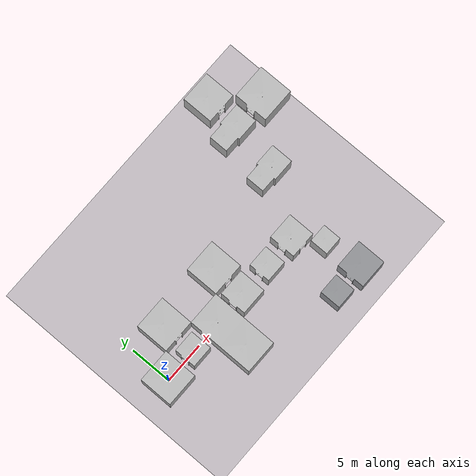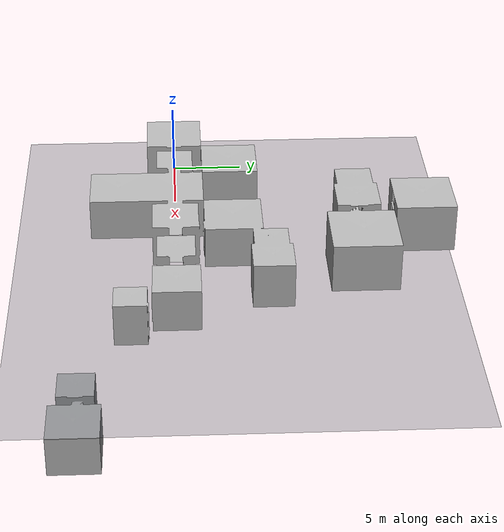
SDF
<?xml version="1.0"?>
<sdf version="1.8">
  <world name="escape_room">
    <gravity>0 0 -9.8</gravity>
    <physics name="default" type="ode">
      <max_step_size>0.004</max_step_size>
      <real_time_factor>1</real_time_factor>
    </physics>

    <plugin filename="libgz-sim-sensors-system.so"
            name="gz::sim::systems::Sensors">
      <render_engine>ogre2</render_engine>
    </plugin>

    <light name="sun" type="directional">
      <pose>0 0 10 0 0 0</pose>
      <diffuse>0.9 0.9 0.85 1</diffuse>
      <specular>0.3 0.3 0.3 1</specular>
      <direction>-0.3 0.2 -1</direction>
    </light>

    <model name="ground">
      <static>true</static>
      <link name="link">
        <collision name="collision">
          <geometry>
            <plane>
              <normal>0 0 1</normal>
              <size>120 120</size>
            </plane>
          </geometry>
        </collision>
        <visual name="visual">
          <geometry>
            <plane>
              <normal>0 0 1</normal>
              <size>120 120</size>
            </plane>
          </geometry>
          <material>
            <ambient>0.15 0.16 0.18 1</ambient>
            <diffuse>0.22 0.24 0.28 1</diffuse>
          </material>
        </visual>
      </link>
    </model>

    <include>
      <uri>model://escape_room_facility</uri>
      <pose>0 0 0 0 0 0</pose>
    </include>

    <include>
      <uri>model://t0_robot</uri>
      <name>t0</name>
      <pose>0.0000 0.0000 0.0500 0 0 0</pose>
    </include>

    <model name="overview_camera">
      <static>true</static>
      <link name="link">
        <pose>14 -10 24 0 0.65 0.85</pose>
        <sensor name="camera" type="camera">
          <camera>
            <horizontal_fov>1.05</horizontal_fov>
            <image><width>1280</width><height>720</height></image>
            <clip><near>0.1</near><far>200</far></clip>
          </camera>
          <topic>/escape_room/camera</topic>
          <update_rate>12</update_rate>
        </sensor>
      </link>
    </model>
  </world>
</sdf>

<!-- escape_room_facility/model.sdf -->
<sdf version="1.8">
  <model name="escape_room_facility">
    <static>true</static>
    <link name="facility">
      <visual name="mesh">
        <geometry>
          <mesh>
            <uri>meshes/escape_room_scene.obj</uri>
            <scale>1 1 1</scale>
          </mesh>
        </geometry>
      </visual>
      <collision name="box_0">
        <pose>12.0000 0.0000 0.0400 0 0 0</pose>
        <geometry>
          <box>
            <size>2.9200 2.9200 0.0800</size>
          </box>
        </geometry>
      </collision>
      <collision name="box_1">
        <pose>12.0000 0.0000 2.9600 0 0 0</pose>
        <geometry>
          <box>
            <size>3.2000 3.2000 0.0800</size>
          </box>
        </geometry>
      </collision>
      <collision name="box_2">
        <pose>12.0000 0.0000 2.9650 0 0 0</pose>
        <geometry>
          <box>
            <size>0.7000 0.3600 0.0500</size>
          </box>
        </geometry>
      </collision>
      <collision name="box_3">
        <pose>11.2800 0.0000 2.9650 0 0 0</pose>
        <geometry>
          <box>
            <size>0.7000 0.3600 0.0500</size>
          </box>
        </geometry>
      </collision>
      <collision name="box_4">
        <pose>12.7200 0.0000 2.9650 0 0 0</pose>
        <geometry>
          <box>
            <size>0.7000 0.3600 0.0500</size>
          </box>
        </geometry>
      </collision>
      <collision name="box_5">
        <pose>10.4000 -1.0625 1.5000 0 0 0</pose>
        <geometry>
          <box>
            <size>0.1400 1.0750 3.0000</size>
          </box>
        </geometry>
      </collision>
      <collision name="box_6">
        <pose>10.4000 1.0625 1.5000 0 0 0</pose>
        <geometry>
          <box>
            <size>0.1400 1.0750 3.0000</size>
          </box>
        </geometry>
      </collision>
      <collision name="box_7">
        <pose>10.4000 -0.4900 1.0750 0 0 0</pose>
        <geometry>
          <box>
            <size>0.1200 0.0700 2.1500</size>
          </box>
        </geometry>
      </collision>
      <collision name="box_8">
        <pose>10.4000 0.4900 1.0750 0 0 0</pose>
        <geometry>
          <box>
            <size>0.1200 0.0700 2.1500</size>
          </box>
        </geometry>
      </collision>
      <collision name="box_9">
        <pose>10.4000 0.0000 2.1150 0 0 0</pose>
        <geometry>
          <box>
            <size>0.1200 1.0500 0.0700</size>
          </box>
        </geometry>
      </collision>
      <collision name="box_10">
        <pose>13.6000 -1.0625 1.5000 0 0 0</pose>
        <geometry>
          <box>
            <size>0.1400 1.0750 3.0000</size>
          </box>
        </geometry>
      </collision>
      <collision name="box_11">
        <pose>13.6000 1.0625 1.5000 0 0 0</pose>
        <geometry>
          <box>
            <size>0.1400 1.0750 3.0000</size>
          </box>
        </geometry>
      </collision>
      <collision name="box_12">
        <pose>13.6000 -0.4900 1.0750 0 0 0</pose>
        <geometry>
          <box>
            <size>0.1200 0.0700 2.1500</size>
          </box>
        </geometry>
      </collision>
      <collision name="box_13">
        <pose>13.6000 0.4900 1.0750 0 0 0</pose>
        <geometry>
          <box>
            <size>0.1200 0.0700 2.1500</size>
          </box>
        </geometry>
      </collision>
      <collision name="box_14">
        <pose>13.6000 0.0000 2.1150 0 0 0</pose>
        <geometry>
          <box>
            <size>0.1200 1.0500 0.0700</size>
          </box>
        </geometry>
      </collision>
      <collision name="box_15">
        <pose>12.0000 -1.6000 1.5000 0 0 0</pose>
        <geometry>
          <box>
            <size>3.2000 0.1400 3.0000</size>
          </box>
        </geometry>
      </collision>
      <collision name="box_16">
        <pose>10.9375 1.6000 1.5000 0 0 0</pose>
        <geometry>
          <box>
            <size>1.0750 0.1400 3.0000</size>
          </box>
        </geometry>
      </collision>
      <collision name="box_17">
        <pose>13.0625 1.6000 1.5000 0 0 0</pose>
        <geometry>
          <box>
            <size>1.0750 0.1400 3.0000</size>
          </box>
        </geometry>
      </collision>
      <collision name="box_18">
        <pose>11.5100 1.6000 1.0750 0 0 0</pose>
        <geometry>
          <box>
            <size>0.0700 0.1200 2.1500</size>
          </box>
        </geometry>
      </collision>
      <collision name="box_19">
        <pose>12.4900 1.6000 1.0750 0 0 0</pose>
        <geometry>
          <box>
            <size>0.0700 0.1200 2.1500</size>
          </box>
        </geometry>
      </collision>
      <collision name="box_20">
        <pose>12.0000 1.6000 2.1150 0 0 0</pose>
        <geometry>
          <box>
            <size>1.0500 0.1200 0.0700</size>
          </box>
        </geometry>
      </collision>
      <collision name="box_21">
        <pose>20.0000 -7.0000 -8.3600 0 0 0</pose>
        <geometry>
          <box>
            <size>2.3200 2.3200 0.0800</size>
          </box>
        </geometry>
      </collision>
      <collision name="box_22">
        <pose>20.0000 -7.0000 -5.4400 0 0 0</pose>
        <geometry>
          <box>
            <size>2.6000 2.6000 0.0800</size>
          </box>
        </geometry>
      </collision>
      <collision name="box_23">
        <pose>20.0000 -7.0000 -5.4350 0 0 0</pose>
        <geometry>
          <box>
            <size>0.7000 0.3600 0.0500</size>
          </box>
        </geometry>
      </collision>
      <collision name="box_24">
        <pose>19.4150 -7.0000 -5.4350 0 0 0</pose>
        <geometry>
          <box>
            <size>0.7000 0.3600 0.0500</size>
          </box>
        </geometry>
      </collision>
      <collision name="box_25">
        <pose>20.5850 -7.0000 -5.4350 0 0 0</pose>
        <geometry>
          <box>
            <size>0.7000 0.3600 0.0500</size>
          </box>
        </geometry>
      </collision>
      <collision name="box_26">
        <pose>18.7000 -7.0000 -6.9000 0 0 0</pose>
        <geometry>
          <box>
            <size>0.1400 2.6000 3.0000</size>
          </box>
        </geometry>
      </collision>
      <collision name="box_27">
        <pose>21.3000 -7.9125 -6.9000 0 0 0</pose>
        <geometry>
          <box>
            <size>0.1400 0.7750 3.0000</size>
          </box>
        </geometry>
      </collision>
      <collision name="box_28">
        <pose>21.3000 -6.0875 -6.9000 0 0 0</pose>
        <geometry>
          <box>
            <size>0.1400 0.7750 3.0000</size>
          </box>
        </geometry>
      </collision>
      <collision name="box_29">
        <pose>21.3000 -7.4900 -7.3250 0 0 0</pose>
        <geometry>
          <box>
            <size>0.1200 0.0700 2.1500</size>
          </box>
        </geometry>
      </collision>
      <collision name="box_30">
        <pose>21.3000 -6.5100 -7.3250 0 0 0</pose>
        <geometry>
          <box>
            <size>0.1200 0.0700 2.1500</size>
          </box>
        </geometry>
      </collision>
      <collision name="box_31">
        <pose>21.3000 -7.0000 -6.2850 0 0 0</pose>
        <geometry>
          <box>
            <size>0.1200 1.0500 0.0700</size>
          </box>
        </geometry>
      </collision>
      <collision name="box_32">
        <pose>20.0000 -8.3000 -6.9000 0 0 0</pose>
        <geometry>
          <box>
            <size>2.6000 0.1400 3.0000</size>
          </box>
        </geometry>
      </collision>
      <collision name="box_33">
        <pose>20.0000 -5.7000 -6.9000 0 0 0</pose>
        <geometry>
          <box>
            <size>2.6000 0.1400 3.0000</size>
          </box>
        </geometry>
      </collision>
      <collision name="box_34">
        <pose>19.5000 -7.0000 -7.6500 0 0 0</pose>
        <geometry>
          <box>
            <size>0.4500 0.8000 0.5000</size>
          </box>
        </geometry>
      </collision>
      <collision name="box_35">
        <pose>20.6000 -7.0000 -7.6500 0 0 0</pose>
        <geometry>
          <box>
            <size>0.4500 0.8000 0.5000</size>
          </box>
        </geometry>
      </collision>
      <collision name="box_36">
        <pose>28.0000 11.0000 8.4400 0 0 0</pose>
        <geometry>
          <box>
            <size>3.7200 3.7200 0.0800</size>
          </box>
        </geometry>
      </collision>
      <collision name="box_37">
        <pose>28.0000 11.0000 11.3600 0 0 0</pose>
        <geometry>
          <box>
            <size>4.0000 4.0000 0.0800</size>
          </box>
        </geometry>
      </collision>
      <collision name="box_38">
        <pose>28.0000 11.0000 11.3650 0 0 0</pose>
        <geometry>
          <box>
            <size>0.7000 0.3600 0.0500</size>
          </box>
        </geometry>
      </collision>
      <collision name="box_39">
        <pose>27.1000 11.0000 11.3650 0 0 0</pose>
        <geometry>
          <box>
            <size>0.7000 0.3600 0.0500</size>
          </box>
        </geometry>
      </collision>
      <collision name="box_40">
        <pose>28.9000 11.0000 11.3650 0 0 0</pose>
        <geometry>
          <box>
            <size>0.7000 0.3600 0.0500</size>
          </box>
        </geometry>
      </collision>
      <collision name="box_41">
        <pose>26.0000 9.7375 9.9000 0 0 0</pose>
        <geometry>
          <box>
            <size>0.1400 1.4750 3.0000</size>
          </box>
        </geometry>
      </collision>
      <collision name="box_42">
        <pose>26.0000 12.2625 9.9000 0 0 0</pose>
        <geometry>
          <box>
            <size>0.1400 1.4750 3.0000</size>
          </box>
        </geometry>
      </collision>
      <collision name="box_43">
        <pose>26.0000 10.5100 9.4750 0 0 0</pose>
        <geometry>
          <box>
            <size>0.1200 0.0700 2.1500</size>
          </box>
        </geometry>
      </collision>
      <collision name="box_44">
        <pose>26.0000 11.4900 9.4750 0 0 0</pose>
        <geometry>
          <box>
            <size>0.1200 0.0700 2.1500</size>
          </box>
        </geometry>
      </collision>
      <collision name="box_45">
        <pose>26.0000 11.0000 10.5150 0 0 0</pose>
        <geometry>
          <box>
            <size>0.1200 1.0500 0.0700</size>
          </box>
        </geometry>
      </collision>
      <collision name="box_46">
        <pose>30.0000 11.0000 9.9000 0 0 0</pose>
        <geometry>
          <box>
            <size>0.1400 4.0000 3.0000</size>
          </box>
        </geometry>
      </collision>
      <collision name="box_47">
        <pose>28.0000 9.0000 9.9000 0 0 0</pose>
        <geometry>
          <box>
            <size>4.0000 0.1400 3.0000</size>
          </box>
        </geometry>
      </collision>
      <collision name="box_48">
        <pose>28.0000 13.0000 9.9000 0 0 0</pose>
        <geometry>
          <box>
            <size>4.0000 0.1400 3.0000</size>
          </box>
        </geometry>
      </collision>
      <collision name="box_49">
        <pose>28.0000 11.2000 9.7000 0 0 0</pose>
        <geometry>
          <box>
            <size>0.8500 1.8000 0.8000</size>
          </box>
        </geometry>
      </collision>
      <collision name="box_50">
        <pose>27.0000 10.2000 10.6000 0 0 0</pose>
        <geometry>
          <box>
            <size>0.8500 0.4500 1.2000</size>
          </box>
        </geometry>
      </collision>
      <collision name="box_51">
        <pose>29.0000 10.2000 10.6000 0 0 0</pose>
        <geometry>
          <box>
            <size>0.8500 0.4500 1.2000</size>
          </box>
        </geometry>
      </collision>
      <collision name="box_52">
        <pose>16.0000 0.0000 0.0400 0 0 0</pose>
        <geometry>
          <box>
            <size>2.3200 2.3200 0.0800</size>
          </box>
        </geometry>
      </collision>
      <collision name="box_53">
        <pose>16.0000 0.0000 2.9600 0 0 0</pose>
        <geometry>
          <box>
            <size>2.6000 2.6000 0.0800</size>
          </box>
        </geometry>
      </collision>
      <collision name="box_54">
        <pose>16.0000 0.0000 2.9650 0 0 0</pose>
        <geometry>
          <box>
            <size>0.7000 0.3600 0.0500</size>
          </box>
        </geometry>
      </collision>
      <collision name="box_55">
        <pose>15.4150 0.0000 2.9650 0 0 0</pose>
        <geometry>
          <box>
            <size>0.7000 0.3600 0.0500</size>
          </box>
        </geometry>
      </collision>
      <collision name="box_56">
        <pose>16.5850 0.0000 2.9650 0 0 0</pose>
        <geometry>
          <box>
            <size>0.7000 0.3600 0.0500</size>
          </box>
        </geometry>
      </collision>
      <collision name="box_57">
        <pose>14.7000 -0.9125 1.5000 0 0 0</pose>
        <geometry>
          <box>
            <size>0.1400 0.7750 3.0000</size>
          </box>
        </geometry>
      </collision>
      <collision name="box_58">
        <pose>14.7000 0.9125 1.5000 0 0 0</pose>
        <geometry>
          <box>
            <size>0.1400 0.7750 3.0000</size>
          </box>
        </geometry>
      </collision>
      <collision name="box_59">
        <pose>14.7000 -0.4900 1.0750 0 0 0</pose>
        <geometry>
          <box>
            <size>0.1200 0.0700 2.1500</size>
          </box>
        </geometry>
      </collision>
      <collision name="box_60">
        <pose>14.7000 0.4900 1.0750 0 0 0</pose>
        <geometry>
          <box>
            <size>0.1200 0.0700 2.1500</size>
          </box>
        </geometry>
      </collision>
      <collision name="box_61">
        <pose>14.7000 0.0000 2.1150 0 0 0</pose>
        <geometry>
          <box>
            <size>0.1200 1.0500 0.0700</size>
          </box>
        </geometry>
      </collision>
      <collision name="box_62">
        <pose>17.3000 -0.9125 1.5000 0 0 0</pose>
        <geometry>
          <box>
            <size>0.1400 0.7750 3.0000</size>
          </box>
        </geometry>
      </collision>
      <collision name="box_63">
        <pose>17.3000 0.9125 1.5000 0 0 0</pose>
        <geometry>
          <box>
            <size>0.1400 0.7750 3.0000</size>
          </box>
        </geometry>
      </collision>
      <collision name="box_64">
        <pose>17.3000 -0.4900 1.0750 0 0 0</pose>
        <geometry>
          <box>
            <size>0.1200 0.0700 2.1500</size>
          </box>
        </geometry>
      </collision>
      <collision name="box_65">
        <pose>17.3000 0.4900 1.0750 0 0 0</pose>
        <geometry>
          <box>
            <size>0.1200 0.0700 2.1500</size>
          </box>
        </geometry>
      </collision>
      <collision name="box_66">
        <pose>17.3000 0.0000 2.1150 0 0 0</pose>
        <geometry>
          <box>
            <size>0.1200 1.0500 0.0700</size>
          </box>
        </geometry>
      </collision>
      <collision name="box_67">
        <pose>16.0000 -1.3000 1.5000 0 0 0</pose>
        <geometry>
          <box>
            <size>2.6000 0.1400 3.0000</size>
          </box>
        </geometry>
      </collision>
      <collision name="box_68">
        <pose>16.0000 1.3000 1.5000 0 0 0</pose>
        <geometry>
          <box>
            <size>2.6000 0.1400 3.0000</size>
          </box>
        </geometry>
      </collision>
      <collision name="box_69">
        <pose>20.0000 0.0000 0.0400 0 0 0</pose>
        <geometry>
          <box>
            <size>2.9200 2.9200 0.0800</size>
          </box>
        </geometry>
      </collision>
      <collision name="box_70">
        <pose>20.0000 0.0000 2.9600 0 0 0</pose>
        <geometry>
          <box>
            <size>3.2000 3.2000 0.0800</size>
          </box>
        </geometry>
      </collision>
      <collision name="box_71">
        <pose>20.0000 0.0000 2.9650 0 0 0</pose>
        <geometry>
          <box>
            <size>0.7000 0.3600 0.0500</size>
          </box>
        </geometry>
      </collision>
      <collision name="box_72">
        <pose>19.2800 0.0000 2.9650 0 0 0</pose>
        <geometry>
          <box>
            <size>0.7000 0.3600 0.0500</size>
          </box>
        </geometry>
      </collision>
      <collision name="box_73">
        <pose>20.7200 0.0000 2.9650 0 0 0</pose>
        <geometry>
          <box>
            <size>0.7000 0.3600 0.0500</size>
          </box>
        </geometry>
      </collision>
      <collision name="box_74">
        <pose>18.4000 -1.0625 1.5000 0 0 0</pose>
        <geometry>
          <box>
            <size>0.1400 1.0750 3.0000</size>
          </box>
        </geometry>
      </collision>
      <collision name="box_75">
        <pose>18.4000 1.0625 1.5000 0 0 0</pose>
        <geometry>
          <box>
            <size>0.1400 1.0750 3.0000</size>
          </box>
        </geometry>
      </collision>
      <collision name="box_76">
        <pose>18.4000 -0.4900 1.0750 0 0 0</pose>
        <geometry>
          <box>
            <size>0.1200 0.0700 2.1500</size>
          </box>
        </geometry>
      </collision>
      <collision name="box_77">
        <pose>18.4000 0.4900 1.0750 0 0 0</pose>
        <geometry>
          <box>
            <size>0.1200 0.0700 2.1500</size>
          </box>
        </geometry>
      </collision>
      <collision name="box_78">
        <pose>18.4000 0.0000 2.1150 0 0 0</pose>
        <geometry>
          <box>
            <size>0.1200 1.0500 0.0700</size>
          </box>
        </geometry>
      </collision>
      <collision name="box_79">
        <pose>21.6000 0.0000 1.5000 0 0 0</pose>
        <geometry>
          <box>
            <size>0.1400 3.2000 3.0000</size>
          </box>
        </geometry>
      </collision>
      <collision name="box_80">
        <pose>18.9375 -1.6000 1.5000 0 0 0</pose>
        <geometry>
          <box>
            <size>1.0750 0.1400 3.0000</size>
          </box>
        </geometry>
      </collision>
      <collision name="box_81">
        <pose>21.0625 -1.6000 1.5000 0 0 0</pose>
        <geometry>
          <box>
            <size>1.0750 0.1400 3.0000</size>
          </box>
        </geometry>
      </collision>
      <collision name="box_82">
        <pose>19.5100 -1.6000 1.0750 0 0 0</pose>
        <geometry>
          <box>
            <size>0.0700 0.1200 2.1500</size>
          </box>
        </geometry>
      </collision>
      <collision name="box_83">
        <pose>20.4900 -1.6000 1.0750 0 0 0</pose>
        <geometry>
          <box>
            <size>0.0700 0.1200 2.1500</size>
          </box>
        </geometry>
      </collision>
      <collision name="box_84">
        <pose>20.0000 -1.6000 2.1150 0 0 0</pose>
        <geometry>
          <box>
            <size>1.0500 0.1200 0.0700</size>
          </box>
        </geometry>
      </collision>
      <collision name="box_85">
        <pose>20.0000 1.6000 1.5000 0 0 0</pose>
        <geometry>
          <box>
            <size>3.2000 0.1400 3.0000</size>
          </box>
        </geometry>
      </collision>
      <collision name="box_86">
        <pose>20.6000 0.0000 2.2250 0 0 0</pose>
        <geometry>
          <box>
            <size>0.9000 0.9000 0.0500</size>
          </box>
        </geometry>
      </collision>
      <collision name="box_87">
        <pose>19.2000 0.0000 1.5500 0 0 0</pose>
        <geometry>
          <box>
            <size>0.9000 0.3500 0.9000</size>
          </box>
        </geometry>
      </collision>
      <collision name="box_88">
        <pose>24.0000 15.0000 8.4400 0 0 0</pose>
        <geometry>
          <box>
            <size>3.3200 3.3200 0.0800</size>
          </box>
        </geometry>
      </collision>
      <collision name="box_89">
        <pose>24.0000 15.0000 11.3600 0 0 0</pose>
        <geometry>
          <box>
            <size>3.6000 3.6000 0.0800</size>
          </box>
        </geometry>
      </collision>
      <collision name="box_90">
        <pose>24.0000 15.0000 11.3650 0 0 0</pose>
        <geometry>
          <box>
            <size>0.7000 0.3600 0.0500</size>
          </box>
        </geometry>
      </collision>
      <collision name="box_91">
        <pose>23.1900 15.0000 11.3650 0 0 0</pose>
        <geometry>
          <box>
            <size>0.7000 0.3600 0.0500</size>
          </box>
        </geometry>
      </collision>
      <collision name="box_92">
        <pose>24.8100 15.0000 11.3650 0 0 0</pose>
        <geometry>
          <box>
            <size>0.7000 0.3600 0.0500</size>
          </box>
        </geometry>
      </collision>
      <collision name="box_93">
        <pose>22.2000 15.0000 9.9000 0 0 0</pose>
        <geometry>
          <box>
            <size>0.1400 3.6000 3.0000</size>
          </box>
        </geometry>
      </collision>
      <collision name="box_94">
        <pose>25.8000 15.0000 9.9000 0 0 0</pose>
        <geometry>
          <box>
            <size>0.1400 3.6000 3.0000</size>
          </box>
        </geometry>
      </collision>
      <collision name="box_95">
        <pose>22.8375 13.2000 9.9000 0 0 0</pose>
        <geometry>
          <box>
            <size>1.2750 0.1400 3.0000</size>
          </box>
        </geometry>
      </collision>
      <collision name="box_96">
        <pose>25.1625 13.2000 9.9000 0 0 0</pose>
        <geometry>
          <box>
            <size>1.2750 0.1400 3.0000</size>
          </box>
        </geometry>
      </collision>
      <collision name="box_97">
        <pose>23.5100 13.2000 9.4750 0 0 0</pose>
        <geometry>
          <box>
            <size>0.0700 0.1200 2.1500</size>
          </box>
        </geometry>
      </collision>
      <collision name="box_98">
        <pose>24.4900 13.2000 9.4750 0 0 0</pose>
        <geometry>
          <box>
            <size>0.0700 0.1200 2.1500</size>
          </box>
        </geometry>
      </collision>
      <collision name="box_99">
        <pose>24.0000 13.2000 10.5150 0 0 0</pose>
        <geometry>
          <box>
            <size>1.0500 0.1200 0.0700</size>
          </box>
        </geometry>
      </collision>
      <collision name="box_100">
        <pose>24.0000 16.8000 9.9000 0 0 0</pose>
        <geometry>
          <box>
            <size>3.6000 0.1400 3.0000</size>
          </box>
        </geometry>
      </collision>
      <collision name="box_101">
        <pose>24.0000 15.5000 10.5600 0 0 0</pose>
        <geometry>
          <box>
            <size>1.0000 1.4000 0.1200</size>
          </box>
        </geometry>
      </collision>
      <collision name="box_102">
        <pose>24.0000 14.4000 9.1000 0 0 0</pose>
        <geometry>
          <box>
            <size>0.9000 0.8000 0.6000</size>
          </box>
        </geometry>
      </collision>
      <collision name="box_103">
        <pose>0.0000 0.0000 0.0400 0 0 0</pose>
        <geometry>
          <box>
            <size>3.7200 3.7200 0.0800</size>
          </box>
        </geometry>
      </collision>
      <collision name="box_104">
        <pose>0.0000 0.0000 2.9600 0 0 0</pose>
        <geometry>
          <box>
            <size>4.0000 4.0000 0.0800</size>
          </box>
        </geometry>
      </collision>
      <collision name="box_105">
        <pose>0.0000 0.0000 2.9650 0 0 0</pose>
        <geometry>
          <box>
            <size>0.7000 0.3600 0.0500</size>
          </box>
        </geometry>
      </collision>
      <collision name="box_106">
        <pose>-0.9000 0.0000 2.9650 0 0 0</pose>
        <geometry>
          <box>
            <size>0.7000 0.3600 0.0500</size>
          </box>
        </geometry>
      </collision>
      <collision name="box_107">
        <pose>0.9000 0.0000 2.9650 0 0 0</pose>
        <geometry>
          <box>
            <size>0.7000 0.3600 0.0500</size>
          </box>
        </geometry>
      </collision>
      <collision name="box_108">
        <pose>-2.0000 0.0000 1.5000 0 0 0</pose>
        <geometry>
          <box>
            <size>0.1400 4.0000 3.0000</size>
          </box>
        </geometry>
      </collision>
      <collision name="box_109">
        <pose>2.0000 -1.2625 1.5000 0 0 0</pose>
        <geometry>
          <box>
            <size>0.1400 1.4750 3.0000</size>
          </box>
        </geometry>
      </collision>
      <collision name="box_110">
        <pose>2.0000 1.2625 1.5000 0 0 0</pose>
        <geometry>
          <box>
            <size>0.1400 1.4750 3.0000</size>
          </box>
        </geometry>
      </collision>
      <collision name="box_111">
        <pose>2.0000 -0.4900 1.0750 0 0 0</pose>
        <geometry>
          <box>
            <size>0.1200 0.0700 2.1500</size>
          </box>
        </geometry>
      </collision>
      <collision name="box_112">
        <pose>2.0000 0.4900 1.0750 0 0 0</pose>
        <geometry>
          <box>
            <size>0.1200 0.0700 2.1500</size>
          </box>
        </geometry>
      </collision>
      <collision name="box_113">
        <pose>2.0000 0.0000 2.1150 0 0 0</pose>
        <geometry>
          <box>
            <size>0.1200 1.0500 0.0700</size>
          </box>
        </geometry>
      </collision>
      <collision name="box_114">
        <pose>0.0000 -2.0000 1.5000 0 0 0</pose>
        <geometry>
          <box>
            <size>4.0000 0.1400 3.0000</size>
          </box>
        </geometry>
      </collision>
      <collision name="box_115">
        <pose>0.0000 2.0000 1.5000 0 0 0</pose>
        <geometry>
          <box>
            <size>4.0000 0.1400 3.0000</size>
          </box>
        </geometry>
      </collision>
      <collision name="box_116">
        <pose>-0.9000 0.0000 0.7250 0 0 0</pose>
        <geometry>
          <box>
            <size>0.3500 1.6000 0.4500</size>
          </box>
        </geometry>
      </collision>
      <collision name="box_117">
        <pose>0.8500 -0.7000 0.9500 0 0 0</pose>
        <geometry>
          <box>
            <size>0.2500 0.1800 1.4000</size>
          </box>
        </geometry>
      </collision>
      <collision name="box_118">
        <pose>0.8500 0.7000 0.9500 0 0 0</pose>
        <geometry>
          <box>
            <size>0.2500 0.1800 1.4000</size>
          </box>
        </geometry>
      </collision>
      <collision name="box_119">
        <pose>8.0000 0.0000 0.0400 0 0 0</pose>
        <geometry>
          <box>
            <size>3.7200 3.7200 0.0800</size>
          </box>
        </geometry>
      </collision>
      <collision name="box_120">
        <pose>8.0000 0.0000 2.9600 0 0 0</pose>
        <geometry>
          <box>
            <size>4.0000 4.0000 0.0800</size>
          </box>
        </geometry>
      </collision>
      <collision name="box_121">
        <pose>8.0000 0.0000 2.9650 0 0 0</pose>
        <geometry>
          <box>
            <size>0.7000 0.3600 0.0500</size>
          </box>
        </geometry>
      </collision>
      <collision name="box_122">
        <pose>7.1000 0.0000 2.9650 0 0 0</pose>
        <geometry>
          <box>
            <size>0.7000 0.3600 0.0500</size>
          </box>
        </geometry>
      </collision>
      <collision name="box_123">
        <pose>8.9000 0.0000 2.9650 0 0 0</pose>
        <geometry>
          <box>
            <size>0.7000 0.3600 0.0500</size>
          </box>
        </geometry>
      </collision>
      <collision name="box_124">
        <pose>6.0000 -1.2625 1.5000 0 0 0</pose>
        <geometry>
          <box>
            <size>0.1400 1.4750 3.0000</size>
          </box>
        </geometry>
      </collision>
      <collision name="box_125">
        <pose>6.0000 1.2625 1.5000 0 0 0</pose>
        <geometry>
          <box>
            <size>0.1400 1.4750 3.0000</size>
          </box>
        </geometry>
      </collision>
      <collision name="box_126">
        <pose>6.0000 -0.4900 1.0750 0 0 0</pose>
        <geometry>
          <box>
            <size>0.1200 0.0700 2.1500</size>
          </box>
        </geometry>
      </collision>
      <collision name="box_127">
        <pose>6.0000 0.4900 1.0750 0 0 0</pose>
        <geometry>
          <box>
            <size>0.1200 0.0700 2.1500</size>
          </box>
        </geometry>
      </collision>
      <collision name="box_128">
        <pose>6.0000 0.0000 2.1150 0 0 0</pose>
        <geometry>
          <box>
            <size>0.1200 1.0500 0.0700</size>
          </box>
        </geometry>
      </collision>
      <collision name="box_129">
        <pose>10.0000 -1.2625 1.5000 0 0 0</pose>
        <geometry>
          <box>
            <size>0.1400 1.4750 3.0000</size>
          </box>
        </geometry>
      </collision>
      <collision name="box_130">
        <pose>10.0000 1.2625 1.5000 0 0 0</pose>
        <geometry>
          <box>
            <size>0.1400 1.4750 3.0000</size>
          </box>
        </geometry>
      </collision>
      <collision name="box_131">
        <pose>10.0000 -0.4900 1.0750 0 0 0</pose>
        <geometry>
          <box>
            <size>0.1200 0.0700 2.1500</size>
          </box>
        </geometry>
      </collision>
      <collision name="box_132">
        <pose>10.0000 0.4900 1.0750 0 0 0</pose>
        <geometry>
          <box>
            <size>0.1200 0.0700 2.1500</size>
          </box>
        </geometry>
      </collision>
      <collision name="box_133">
        <pose>10.0000 0.0000 2.1150 0 0 0</pose>
        <geometry>
          <box>
            <size>0.1200 1.0500 0.0700</size>
          </box>
        </geometry>
      </collision>
      <collision name="box_134">
        <pose>6.7375 -2.0000 1.5000 0 0 0</pose>
        <geometry>
          <box>
            <size>1.4750 0.1400 3.0000</size>
          </box>
        </geometry>
      </collision>
      <collision name="box_135">
        <pose>9.2625 -2.0000 1.5000 0 0 0</pose>
        <geometry>
          <box>
            <size>1.4750 0.1400 3.0000</size>
          </box>
        </geometry>
      </collision>
      <collision name="box_136">
        <pose>7.5100 -2.0000 1.0750 0 0 0</pose>
        <geometry>
          <box>
            <size>0.0700 0.1200 2.1500</size>
          </box>
        </geometry>
      </collision>
      <collision name="box_137">
        <pose>8.4900 -2.0000 1.0750 0 0 0</pose>
        <geometry>
          <box>
            <size>0.0700 0.1200 2.1500</size>
          </box>
        </geometry>
      </collision>
      <collision name="box_138">
        <pose>8.0000 -2.0000 2.1150 0 0 0</pose>
        <geometry>
          <box>
            <size>1.0500 0.1200 0.0700</size>
          </box>
        </geometry>
      </collision>
      <collision name="box_139">
        <pose>8.0000 2.0000 1.5000 0 0 0</pose>
        <geometry>
          <box>
            <size>4.0000 0.1400 3.0000</size>
          </box>
        </geometry>
      </collision>
      <collision name="box_140">
        <pose>8.0000 0.0000 1.2250 0 0 0</pose>
        <geometry>
          <box>
            <size>0.9000 1.4000 0.7500</size>
          </box>
        </geometry>
      </collision>
      <collision name="box_141">
        <pose>7.0000 -1.0000 1.2500 0 0 0</pose>
        <geometry>
          <box>
            <size>0.9000 0.5000 0.5000</size>
          </box>
        </geometry>
      </collision>
      <collision name="box_142">
        <pose>7.0000 1.0000 1.2500 0 0 0</pose>
        <geometry>
          <box>
            <size>0.9000 0.5000 0.5000</size>
          </box>
        </geometry>
      </collision>
      <collision name="box_143">
        <pose>24.0000 -7.0000 -8.3600 0 0 0</pose>
        <geometry>
          <box>
            <size>3.3200 3.3200 0.0800</size>
          </box>
        </geometry>
      </collision>
      <collision name="box_144">
        <pose>24.0000 -7.0000 -5.4400 0 0 0</pose>
        <geometry>
          <box>
            <size>3.6000 3.6000 0.0800</size>
          </box>
        </geometry>
      </collision>
      <collision name="box_145">
        <pose>24.0000 -7.0000 -5.4350 0 0 0</pose>
        <geometry>
          <box>
            <size>0.7000 0.3600 0.0500</size>
          </box>
        </geometry>
      </collision>
      <collision name="box_146">
        <pose>23.1900 -7.0000 -5.4350 0 0 0</pose>
        <geometry>
          <box>
            <size>0.7000 0.3600 0.0500</size>
          </box>
        </geometry>
      </collision>
      <collision name="box_147">
        <pose>24.8100 -7.0000 -5.4350 0 0 0</pose>
        <geometry>
          <box>
            <size>0.7000 0.3600 0.0500</size>
          </box>
        </geometry>
      </collision>
      <collision name="box_148">
        <pose>22.2000 -8.1625 -6.9000 0 0 0</pose>
        <geometry>
          <box>
            <size>0.1400 1.2750 3.0000</size>
          </box>
        </geometry>
      </collision>
      <collision name="box_149">
        <pose>22.2000 -5.8375 -6.9000 0 0 0</pose>
        <geometry>
          <box>
            <size>0.1400 1.2750 3.0000</size>
          </box>
        </geometry>
      </collision>
      <collision name="box_150">
        <pose>22.2000 -7.4900 -7.3250 0 0 0</pose>
        <geometry>
          <box>
            <size>0.1200 0.0700 2.1500</size>
          </box>
        </geometry>
      </collision>
      <collision name="box_151">
        <pose>22.2000 -6.5100 -7.3250 0 0 0</pose>
        <geometry>
          <box>
            <size>0.1200 0.0700 2.1500</size>
          </box>
        </geometry>
      </collision>
      <collision name="box_152">
        <pose>22.2000 -7.0000 -6.2850 0 0 0</pose>
        <geometry>
          <box>
            <size>0.1200 1.0500 0.0700</size>
          </box>
        </geometry>
      </collision>
      <collision name="box_153">
        <pose>25.8000 -7.0000 -6.9000 0 0 0</pose>
        <geometry>
          <box>
            <size>0.1400 3.6000 3.0000</size>
          </box>
        </geometry>
      </collision>
      <collision name="box_154">
        <pose>24.0000 -8.8000 -6.9000 0 0 0</pose>
        <geometry>
          <box>
            <size>3.6000 0.1400 3.0000</size>
          </box>
        </geometry>
      </collision>
      <collision name="box_155">
        <pose>24.0000 -5.2000 -6.9000 0 0 0</pose>
        <geometry>
          <box>
            <size>3.6000 0.1400 3.0000</size>
          </box>
        </geometry>
      </collision>
      <collision name="box_156">
        <pose>24.0000 -6.6000 -6.3500 0 0 0</pose>
        <geometry>
          <box>
            <size>1.0000 1.2000 0.1000</size>
          </box>
        </geometry>
      </collision>
      <collision name="box_157">
        <pose>24.0000 6.0000 4.2400 0 0 0</pose>
        <geometry>
          <box>
            <size>2.3200 2.3200 0.0800</size>
          </box>
        </geometry>
      </collision>
      <collision name="box_158">
        <pose>24.0000 6.0000 7.1600 0 0 0</pose>
        <geometry>
          <box>
            <size>2.6000 2.6000 0.0800</size>
          </box>
        </geometry>
      </collision>
      <collision name="box_159">
        <pose>24.0000 6.0000 7.1650 0 0 0</pose>
        <geometry>
          <box>
            <size>0.7000 0.3600 0.0500</size>
          </box>
        </geometry>
      </collision>
      <collision name="box_160">
        <pose>23.4150 6.0000 7.1650 0 0 0</pose>
        <geometry>
          <box>
            <size>0.7000 0.3600 0.0500</size>
          </box>
        </geometry>
      </collision>
      <collision name="box_161">
        <pose>24.5850 6.0000 7.1650 0 0 0</pose>
        <geometry>
          <box>
            <size>0.7000 0.3600 0.0500</size>
          </box>
        </geometry>
      </collision>
      <collision name="box_162">
        <pose>22.7000 5.0875 5.7000 0 0 0</pose>
        <geometry>
          <box>
            <size>0.1400 0.7750 3.0000</size>
          </box>
        </geometry>
      </collision>
      <collision name="box_163">
        <pose>22.7000 6.9125 5.7000 0 0 0</pose>
        <geometry>
          <box>
            <size>0.1400 0.7750 3.0000</size>
          </box>
        </geometry>
      </collision>
      <collision name="box_164">
        <pose>22.7000 5.5100 5.2750 0 0 0</pose>
        <geometry>
          <box>
            <size>0.1200 0.0700 2.1500</size>
          </box>
        </geometry>
      </collision>
      <collision name="box_165">
        <pose>22.7000 6.4900 5.2750 0 0 0</pose>
        <geometry>
          <box>
            <size>0.1200 0.0700 2.1500</size>
          </box>
        </geometry>
      </collision>
      <collision name="box_166">
        <pose>22.7000 6.0000 6.3150 0 0 0</pose>
        <geometry>
          <box>
            <size>0.1200 1.0500 0.0700</size>
          </box>
        </geometry>
      </collision>
      <collision name="box_167">
        <pose>25.3000 6.0000 5.7000 0 0 0</pose>
        <geometry>
          <box>
            <size>0.1400 2.6000 3.0000</size>
          </box>
        </geometry>
      </collision>
      <collision name="box_168">
        <pose>24.0000 4.7000 5.7000 0 0 0</pose>
        <geometry>
          <box>
            <size>2.6000 0.1400 3.0000</size>
          </box>
        </geometry>
      </collision>
      <collision name="box_169">
        <pose>24.0000 7.3000 5.7000 0 0 0</pose>
        <geometry>
          <box>
            <size>2.6000 0.1400 3.0000</size>
          </box>
        </geometry>
      </collision>
      <collision name="box_170">
        <pose>8.0000 -4.0000 0.0400 0 0 0</pose>
        <geometry>
          <box>
            <size>3.7200 3.7200 0.0800</size>
          </box>
        </geometry>
      </collision>
      <collision name="box_171">
        <pose>8.0000 -4.0000 2.9600 0 0 0</pose>
        <geometry>
          <box>
            <size>4.0000 4.0000 0.0800</size>
          </box>
        </geometry>
      </collision>
      <collision name="box_172">
        <pose>8.0000 -4.0000 2.9650 0 0 0</pose>
        <geometry>
          <box>
            <size>0.7000 0.3600 0.0500</size>
          </box>
        </geometry>
      </collision>
      <collision name="box_173">
        <pose>7.1000 -4.0000 2.9650 0 0 0</pose>
        <geometry>
          <box>
            <size>0.7000 0.3600 0.0500</size>
          </box>
        </geometry>
      </collision>
      <collision name="box_174">
        <pose>8.9000 -4.0000 2.9650 0 0 0</pose>
        <geometry>
          <box>
            <size>0.7000 0.3600 0.0500</size>
          </box>
        </geometry>
      </collision>
      <collision name="box_175">
        <pose>6.0000 -4.0000 1.5000 0 0 0</pose>
        <geometry>
          <box>
            <size>0.1400 4.0000 3.0000</size>
          </box>
        </geometry>
      </collision>
      <collision name="box_176">
        <pose>10.0000 -4.0000 1.5000 0 0 0</pose>
        <geometry>
          <box>
            <size>0.1400 4.0000 3.0000</size>
          </box>
        </geometry>
      </collision>
      <collision name="box_177">
        <pose>8.0000 -6.0000 1.5000 0 0 0</pose>
        <geometry>
          <box>
            <size>4.0000 0.1400 3.0000</size>
          </box>
        </geometry>
      </collision>
      <collision name="box_178">
        <pose>6.7375 -2.0000 1.5000 0 0 0</pose>
        <geometry>
          <box>
            <size>1.4750 0.1400 3.0000</size>
          </box>
        </geometry>
      </collision>
      <collision name="box_179">
        <pose>9.2625 -2.0000 1.5000 0 0 0</pose>
        <geometry>
          <box>
            <size>1.4750 0.1400 3.0000</size>
          </box>
        </geometry>
      </collision>
      <collision name="box_180">
        <pose>7.5100 -2.0000 1.0750 0 0 0</pose>
        <geometry>
          <box>
            <size>0.0700 0.1200 2.1500</size>
          </box>
        </geometry>
      </collision>
      <collision name="box_181">
        <pose>8.4900 -2.0000 1.0750 0 0 0</pose>
        <geometry>
          <box>
            <size>0.0700 0.1200 2.1500</size>
          </box>
        </geometry>
      </collision>
      <collision name="box_182">
        <pose>8.0000 -2.0000 2.1150 0 0 0</pose>
        <geometry>
          <box>
            <size>1.0500 0.1200 0.0700</size>
          </box>
        </geometry>
      </collision>
      <collision name="box_183">
        <pose>8.2000 -4.0000 1.1250 0 0 0</pose>
        <geometry>
          <box>
            <size>0.7500 1.2000 0.7500</size>
          </box>
        </geometry>
      </collision>
      <collision name="box_184">
        <pose>6.9000 -4.0000 1.8500 0 0 0</pose>
        <geometry>
          <box>
            <size>0.7500 0.3500 0.9000</size>
          </box>
        </geometry>
      </collision>
      <collision name="box_185">
        <pose>9.0000 -5.0000 0.7750 0 0 0</pose>
        <geometry>
          <box>
            <size>0.7500 0.5500 0.4500</size>
          </box>
        </geometry>
      </collision>
      <collision name="box_186">
        <pose>4.0000 4.0000 0.0400 0 0 0</pose>
        <geometry>
          <box>
            <size>3.7200 3.7200 0.0800</size>
          </box>
        </geometry>
      </collision>
      <collision name="box_187">
        <pose>4.0000 4.0000 2.9600 0 0 0</pose>
        <geometry>
          <box>
            <size>4.0000 4.0000 0.0800</size>
          </box>
        </geometry>
      </collision>
      <collision name="box_188">
        <pose>4.0000 4.0000 2.9650 0 0 0</pose>
        <geometry>
          <box>
            <size>0.7000 0.3600 0.0500</size>
          </box>
        </geometry>
      </collision>
      <collision name="box_189">
        <pose>3.1000 4.0000 2.9650 0 0 0</pose>
        <geometry>
          <box>
            <size>0.7000 0.3600 0.0500</size>
          </box>
        </geometry>
      </collision>
      <collision name="box_190">
        <pose>4.9000 4.0000 2.9650 0 0 0</pose>
        <geometry>
          <box>
            <size>0.7000 0.3600 0.0500</size>
          </box>
        </geometry>
      </collision>
      <collision name="box_191">
        <pose>2.0000 4.0000 1.5000 0 0 0</pose>
        <geometry>
          <box>
            <size>0.1400 4.0000 3.0000</size>
          </box>
        </geometry>
      </collision>
      <collision name="box_192">
        <pose>6.0000 4.0000 1.5000 0 0 0</pose>
        <geometry>
          <box>
            <size>0.1400 4.0000 3.0000</size>
          </box>
        </geometry>
      </collision>
      <collision name="box_193">
        <pose>2.7375 2.0000 1.5000 0 0 0</pose>
        <geometry>
          <box>
            <size>1.4750 0.1400 3.0000</size>
          </box>
        </geometry>
      </collision>
      <collision name="box_194">
        <pose>5.2625 2.0000 1.5000 0 0 0</pose>
        <geometry>
          <box>
            <size>1.4750 0.1400 3.0000</size>
          </box>
        </geometry>
      </collision>
      <collision name="box_195">
        <pose>3.5100 2.0000 1.0750 0 0 0</pose>
        <geometry>
          <box>
            <size>0.0700 0.1200 2.1500</size>
          </box>
        </geometry>
      </collision>
      <collision name="box_196">
        <pose>4.4900 2.0000 1.0750 0 0 0</pose>
        <geometry>
          <box>
            <size>0.0700 0.1200 2.1500</size>
          </box>
        </geometry>
      </collision>
      <collision name="box_197">
        <pose>4.0000 2.0000 2.1150 0 0 0</pose>
        <geometry>
          <box>
            <size>1.0500 0.1200 0.0700</size>
          </box>
        </geometry>
      </collision>
      <collision name="box_198">
        <pose>4.0000 6.0000 1.5000 0 0 0</pose>
        <geometry>
          <box>
            <size>4.0000 0.1400 3.0000</size>
          </box>
        </geometry>
      </collision>
      <collision name="box_199">
        <pose>3.1000 3.2000 2.0750 0 0 0</pose>
        <geometry>
          <box>
            <size>0.9000 0.4500 0.5500</size>
          </box>
        </geometry>
      </collision>
      <collision name="box_200">
        <pose>3.1000 4.0000 2.0750 0 0 0</pose>
        <geometry>
          <box>
            <size>0.9000 0.4500 0.5500</size>
          </box>
        </geometry>
      </collision>
      <collision name="box_201">
        <pose>3.1000 4.8000 2.0750 0 0 0</pose>
        <geometry>
          <box>
            <size>0.9000 0.4500 0.5500</size>
          </box>
        </geometry>
      </collision>
      <collision name="box_202">
        <pose>4.5000 4.0000 1.1000 0 0 0</pose>
        <geometry>
          <box>
            <size>0.9000 0.6000 0.4000</size>
          </box>
        </geometry>
      </collision>
      <collision name="box_203">
        <pose>22.0000 -3.0000 0.0400 0 0 0</pose>
        <geometry>
          <box>
            <size>1.9200 1.9200 0.0800</size>
          </box>
        </geometry>
      </collision>
      <collision name="box_204">
        <pose>22.0000 -3.0000 2.9600 0 0 0</pose>
        <geometry>
          <box>
            <size>2.2000 2.2000 0.0800</size>
          </box>
        </geometry>
      </collision>
      <collision name="box_205">
        <pose>22.0000 -3.0000 2.9650 0 0 0</pose>
        <geometry>
          <box>
            <size>0.7000 0.3600 0.0500</size>
          </box>
        </geometry>
      </collision>
      <collision name="box_206">
        <pose>21.5050 -3.0000 2.9650 0 0 0</pose>
        <geometry>
          <box>
            <size>0.7000 0.3600 0.0500</size>
          </box>
        </geometry>
      </collision>
      <collision name="box_207">
        <pose>22.4950 -3.0000 2.9650 0 0 0</pose>
        <geometry>
          <box>
            <size>0.7000 0.3600 0.0500</size>
          </box>
        </geometry>
      </collision>
      <collision name="box_208">
        <pose>20.9000 -3.0000 1.5000 0 0 0</pose>
        <geometry>
          <box>
            <size>0.1400 2.2000 3.0000</size>
          </box>
        </geometry>
      </collision>
      <collision name="box_209">
        <pose>23.1000 -3.0000 1.5000 0 0 0</pose>
        <geometry>
          <box>
            <size>0.1400 2.2000 3.0000</size>
          </box>
        </geometry>
      </collision>
      <collision name="box_210">
        <pose>22.0000 -4.1000 1.5000 0 0 0</pose>
        <geometry>
          <box>
            <size>2.2000 0.1400 3.0000</size>
          </box>
        </geometry>
      </collision>
      <collision name="box_211">
        <pose>21.1875 -1.9000 1.5000 0 0 0</pose>
        <geometry>
          <box>
            <size>0.5750 0.1400 3.0000</size>
          </box>
        </geometry>
      </collision>
      <collision name="box_212">
        <pose>22.8125 -1.9000 1.5000 0 0 0</pose>
        <geometry>
          <box>
            <size>0.5750 0.1400 3.0000</size>
          </box>
        </geometry>
      </collision>
      <collision name="box_213">
        <pose>21.5100 -1.9000 1.0750 0 0 0</pose>
        <geometry>
          <box>
            <size>0.0700 0.1200 2.1500</size>
          </box>
        </geometry>
      </collision>
      <collision name="box_214">
        <pose>22.4900 -1.9000 1.0750 0 0 0</pose>
        <geometry>
          <box>
            <size>0.0700 0.1200 2.1500</size>
          </box>
        </geometry>
      </collision>
      <collision name="box_215">
        <pose>22.0000 -1.9000 2.1150 0 0 0</pose>
        <geometry>
          <box>
            <size>1.0500 0.1200 0.0700</size>
          </box>
        </geometry>
      </collision>
      <collision name="box_216">
        <pose>22.0000 -3.3520 0.0600 0 0 0</pose>
        <geometry>
          <box>
            <size>1.1000 0.1760 0.1200</size>
          </box>
        </geometry>
      </collision>
      <collision name="box_217">
        <pose>22.0000 -3.1760 0.1800 0 0 0</pose>
        <geometry>
          <box>
            <size>1.1000 0.1760 0.1200</size>
          </box>
        </geometry>
      </collision>
      <collision name="box_218">
        <pose>22.0000 -3.0000 0.3000 0 0 0</pose>
        <geometry>
          <box>
            <size>1.1000 0.1760 0.1200</size>
          </box>
        </geometry>
      </collision>
      <collision name="box_219">
        <pose>22.0000 -2.8240 0.4200 0 0 0</pose>
        <geometry>
          <box>
            <size>1.1000 0.1760 0.1200</size>
          </box>
        </geometry>
      </collision>
      <collision name="box_220">
        <pose>22.0000 -2.6480 0.5400 0 0 0</pose>
        <geometry>
          <box>
            <size>1.1000 0.1760 0.1200</size>
          </box>
        </geometry>
      </collision>
      <collision name="box_221">
        <pose>22.0000 6.0000 4.2400 0 0 0</pose>
        <geometry>
          <box>
            <size>1.9200 1.9200 0.0800</size>
          </box>
        </geometry>
      </collision>
      <collision name="box_222">
        <pose>22.0000 6.0000 7.1600 0 0 0</pose>
        <geometry>
          <box>
            <size>2.2000 2.2000 0.0800</size>
          </box>
        </geometry>
      </collision>
      <collision name="box_223">
        <pose>22.0000 6.0000 7.1650 0 0 0</pose>
        <geometry>
          <box>
            <size>0.7000 0.3600 0.0500</size>
          </box>
        </geometry>
      </collision>
      <collision name="box_224">
        <pose>21.5050 6.0000 7.1650 0 0 0</pose>
        <geometry>
          <box>
            <size>0.7000 0.3600 0.0500</size>
          </box>
        </geometry>
      </collision>
      <collision name="box_225">
        <pose>22.4950 6.0000 7.1650 0 0 0</pose>
        <geometry>
          <box>
            <size>0.7000 0.3600 0.0500</size>
          </box>
        </geometry>
      </collision>
      <collision name="box_226">
        <pose>20.9000 6.0000 5.7000 0 0 0</pose>
        <geometry>
          <box>
            <size>0.1400 2.2000 3.0000</size>
          </box>
        </geometry>
      </collision>
      <collision name="box_227">
        <pose>23.1000 5.1875 5.7000 0 0 0</pose>
        <geometry>
          <box>
            <size>0.1400 0.5750 3.0000</size>
          </box>
        </geometry>
      </collision>
      <collision name="box_228">
        <pose>23.1000 6.8125 5.7000 0 0 0</pose>
        <geometry>
          <box>
            <size>0.1400 0.5750 3.0000</size>
          </box>
        </geometry>
      </collision>
      <collision name="box_229">
        <pose>23.1000 5.5100 5.2750 0 0 0</pose>
        <geometry>
          <box>
            <size>0.1200 0.0700 2.1500</size>
          </box>
        </geometry>
      </collision>
      <collision name="box_230">
        <pose>23.1000 6.4900 5.2750 0 0 0</pose>
        <geometry>
          <box>
            <size>0.1200 0.0700 2.1500</size>
          </box>
        </geometry>
      </collision>
      <collision name="box_231">
        <pose>23.1000 6.0000 6.3150 0 0 0</pose>
        <geometry>
          <box>
            <size>0.1200 1.0500 0.0700</size>
          </box>
        </geometry>
      </collision>
      <collision name="box_232">
        <pose>22.0000 4.9000 5.7000 0 0 0</pose>
        <geometry>
          <box>
            <size>2.2000 0.1400 3.0000</size>
          </box>
        </geometry>
      </collision>
      <collision name="box_233">
        <pose>22.0000 7.1000 5.7000 0 0 0</pose>
        <geometry>
          <box>
            <size>2.2000 0.1400 3.0000</size>
          </box>
        </geometry>
      </collision>
      <collision name="box_234">
        <pose>22.0000 5.6480 4.2600 0 0 0</pose>
        <geometry>
          <box>
            <size>1.1000 0.1760 0.1200</size>
          </box>
        </geometry>
      </collision>
      <collision name="box_235">
        <pose>22.0000 5.8240 4.3800 0 0 0</pose>
        <geometry>
          <box>
            <size>1.1000 0.1760 0.1200</size>
          </box>
        </geometry>
      </collision>
      <collision name="box_236">
        <pose>22.0000 6.0000 4.5000 0 0 0</pose>
        <geometry>
          <box>
            <size>1.1000 0.1760 0.1200</size>
          </box>
        </geometry>
      </collision>
      <collision name="box_237">
        <pose>22.0000 6.1760 4.6200 0 0 0</pose>
        <geometry>
          <box>
            <size>1.1000 0.1760 0.1200</size>
          </box>
        </geometry>
      </collision>
      <collision name="box_238">
        <pose>22.0000 6.3520 4.7400 0 0 0</pose>
        <geometry>
          <box>
            <size>1.1000 0.1760 0.1200</size>
          </box>
        </geometry>
      </collision>
      <collision name="box_239">
        <pose>22.0000 11.0000 8.4400 0 0 0</pose>
        <geometry>
          <box>
            <size>1.9200 1.9200 0.0800</size>
          </box>
        </geometry>
      </collision>
      <collision name="box_240">
        <pose>22.0000 11.0000 11.3600 0 0 0</pose>
        <geometry>
          <box>
            <size>2.2000 2.2000 0.0800</size>
          </box>
        </geometry>
      </collision>
      <collision name="box_241">
        <pose>22.0000 11.0000 11.3650 0 0 0</pose>
        <geometry>
          <box>
            <size>0.7000 0.3600 0.0500</size>
          </box>
        </geometry>
      </collision>
      <collision name="box_242">
        <pose>21.5050 11.0000 11.3650 0 0 0</pose>
        <geometry>
          <box>
            <size>0.7000 0.3600 0.0500</size>
          </box>
        </geometry>
      </collision>
      <collision name="box_243">
        <pose>22.4950 11.0000 11.3650 0 0 0</pose>
        <geometry>
          <box>
            <size>0.7000 0.3600 0.0500</size>
          </box>
        </geometry>
      </collision>
      <collision name="box_244">
        <pose>20.9000 11.0000 9.9000 0 0 0</pose>
        <geometry>
          <box>
            <size>0.1400 2.2000 3.0000</size>
          </box>
        </geometry>
      </collision>
      <collision name="box_245">
        <pose>23.1000 10.1875 9.9000 0 0 0</pose>
        <geometry>
          <box>
            <size>0.1400 0.5750 3.0000</size>
          </box>
        </geometry>
      </collision>
      <collision name="box_246">
        <pose>23.1000 11.8125 9.9000 0 0 0</pose>
        <geometry>
          <box>
            <size>0.1400 0.5750 3.0000</size>
          </box>
        </geometry>
      </collision>
      <collision name="box_247">
        <pose>23.1000 10.5100 9.4750 0 0 0</pose>
        <geometry>
          <box>
            <size>0.1200 0.0700 2.1500</size>
          </box>
        </geometry>
      </collision>
      <collision name="box_248">
        <pose>23.1000 11.4900 9.4750 0 0 0</pose>
        <geometry>
          <box>
            <size>0.1200 0.0700 2.1500</size>
          </box>
        </geometry>
      </collision>
      <collision name="box_249">
        <pose>23.1000 11.0000 10.5150 0 0 0</pose>
        <geometry>
          <box>
            <size>0.1200 1.0500 0.0700</size>
          </box>
        </geometry>
      </collision>
      <collision name="box_250">
        <pose>22.0000 9.9000 9.9000 0 0 0</pose>
        <geometry>
          <box>
            <size>2.2000 0.1400 3.0000</size>
          </box>
        </geometry>
      </collision>
      <collision name="box_251">
        <pose>22.0000 12.1000 9.9000 0 0 0</pose>
        <geometry>
          <box>
            <size>2.2000 0.1400 3.0000</size>
          </box>
        </geometry>
      </collision>
      <collision name="box_252">
        <pose>22.0000 10.6480 8.4600 0 0 0</pose>
        <geometry>
          <box>
            <size>1.1000 0.1760 0.1200</size>
          </box>
        </geometry>
      </collision>
      <collision name="box_253">
        <pose>22.0000 10.8240 8.5800 0 0 0</pose>
        <geometry>
          <box>
            <size>1.1000 0.1760 0.1200</size>
          </box>
        </geometry>
      </collision>
      <collision name="box_254">
        <pose>22.0000 11.0000 8.7000 0 0 0</pose>
        <geometry>
          <box>
            <size>1.1000 0.1760 0.1200</size>
          </box>
        </geometry>
      </collision>
      <collision name="box_255">
        <pose>22.0000 11.1760 8.8200 0 0 0</pose>
        <geometry>
          <box>
            <size>1.1000 0.1760 0.1200</size>
          </box>
        </geometry>
      </collision>
      <collision name="box_256">
        <pose>22.0000 11.3520 8.9400 0 0 0</pose>
        <geometry>
          <box>
            <size>1.1000 0.1760 0.1200</size>
          </box>
        </geometry>
      </collision>
      <collision name="box_257">
        <pose>12.0000 4.0000 0.0400 0 0 0</pose>
        <geometry>
          <box>
            <size>3.7200 3.7200 0.0800</size>
          </box>
        </geometry>
      </collision>
      <collision name="box_258">
        <pose>12.0000 4.0000 2.9600 0 0 0</pose>
        <geometry>
          <box>
            <size>4.0000 4.0000 0.0800</size>
          </box>
        </geometry>
      </collision>
      <collision name="box_259">
        <pose>12.0000 4.0000 2.9650 0 0 0</pose>
        <geometry>
          <box>
            <size>0.7000 0.3600 0.0500</size>
          </box>
        </geometry>
      </collision>
      <collision name="box_260">
        <pose>11.1000 4.0000 2.9650 0 0 0</pose>
        <geometry>
          <box>
            <size>0.7000 0.3600 0.0500</size>
          </box>
        </geometry>
      </collision>
      <collision name="box_261">
        <pose>12.9000 4.0000 2.9650 0 0 0</pose>
        <geometry>
          <box>
            <size>0.7000 0.3600 0.0500</size>
          </box>
        </geometry>
      </collision>
      <collision name="box_262">
        <pose>10.0000 4.0000 1.5000 0 0 0</pose>
        <geometry>
          <box>
            <size>0.1400 4.0000 3.0000</size>
          </box>
        </geometry>
      </collision>
      <collision name="box_263">
        <pose>14.0000 4.0000 1.5000 0 0 0</pose>
        <geometry>
          <box>
            <size>0.1400 4.0000 3.0000</size>
          </box>
        </geometry>
      </collision>
      <collision name="box_264">
        <pose>10.7375 2.0000 1.5000 0 0 0</pose>
        <geometry>
          <box>
            <size>1.4750 0.1400 3.0000</size>
          </box>
        </geometry>
      </collision>
      <collision name="box_265">
        <pose>13.2625 2.0000 1.5000 0 0 0</pose>
        <geometry>
          <box>
            <size>1.4750 0.1400 3.0000</size>
          </box>
        </geometry>
      </collision>
      <collision name="box_266">
        <pose>11.5100 2.0000 1.0750 0 0 0</pose>
        <geometry>
          <box>
            <size>0.0700 0.1200 2.1500</size>
          </box>
        </geometry>
      </collision>
      <collision name="box_267">
        <pose>12.4900 2.0000 1.0750 0 0 0</pose>
        <geometry>
          <box>
            <size>0.0700 0.1200 2.1500</size>
          </box>
        </geometry>
      </collision>
      <collision name="box_268">
        <pose>12.0000 2.0000 2.1150 0 0 0</pose>
        <geometry>
          <box>
            <size>1.0500 0.1200 0.0700</size>
          </box>
        </geometry>
      </collision>
      <collision name="box_269">
        <pose>12.0000 6.0000 1.5000 0 0 0</pose>
        <geometry>
          <box>
            <size>4.0000 0.1400 3.0000</size>
          </box>
        </geometry>
      </collision>
      <collision name="box_270">
        <pose>11.2000 3.2000 1.6500 0 0 0</pose>
        <geometry>
          <box>
            <size>0.5500 0.9000 0.9000</size>
          </box>
        </geometry>
      </collision>
      <collision name="box_271">
        <pose>12.8000 3.2000 1.6500 0 0 0</pose>
        <geometry>
          <box>
            <size>0.5500 0.9000 0.9000</size>
          </box>
        </geometry>
      </collision>
      <collision name="box_272">
        <pose>12.0000 4.9000 1.0500 0 0 0</pose>
        <geometry>
          <box>
            <size>0.5500 1.6000 0.7000</size>
          </box>
        </geometry>
      </collision>
      <collision name="box_273">
        <pose>24.0000 11.0000 8.4400 0 0 0</pose>
        <geometry>
          <box>
            <size>2.3200 2.3200 0.0800</size>
          </box>
        </geometry>
      </collision>
      <collision name="box_274">
        <pose>24.0000 11.0000 11.3600 0 0 0</pose>
        <geometry>
          <box>
            <size>2.6000 2.6000 0.0800</size>
          </box>
        </geometry>
      </collision>
      <collision name="box_275">
        <pose>24.0000 11.0000 11.3650 0 0 0</pose>
        <geometry>
          <box>
            <size>0.7000 0.3600 0.0500</size>
          </box>
        </geometry>
      </collision>
      <collision name="box_276">
        <pose>23.4150 11.0000 11.3650 0 0 0</pose>
        <geometry>
          <box>
            <size>0.7000 0.3600 0.0500</size>
          </box>
        </geometry>
      </collision>
      <collision name="box_277">
        <pose>24.5850 11.0000 11.3650 0 0 0</pose>
        <geometry>
          <box>
            <size>0.7000 0.3600 0.0500</size>
          </box>
        </geometry>
      </collision>
      <collision name="box_278">
        <pose>22.7000 10.0875 9.9000 0 0 0</pose>
        <geometry>
          <box>
            <size>0.1400 0.7750 3.0000</size>
          </box>
        </geometry>
      </collision>
      <collision name="box_279">
        <pose>22.7000 11.9125 9.9000 0 0 0</pose>
        <geometry>
          <box>
            <size>0.1400 0.7750 3.0000</size>
          </box>
        </geometry>
      </collision>
      <collision name="box_280">
        <pose>22.7000 10.5100 9.4750 0 0 0</pose>
        <geometry>
          <box>
            <size>0.1200 0.0700 2.1500</size>
          </box>
        </geometry>
      </collision>
      <collision name="box_281">
        <pose>22.7000 11.4900 9.4750 0 0 0</pose>
        <geometry>
          <box>
            <size>0.1200 0.0700 2.1500</size>
          </box>
        </geometry>
      </collision>
      <collision name="box_282">
        <pose>22.7000 11.0000 10.5150 0 0 0</pose>
        <geometry>
          <box>
            <size>0.1200 1.0500 0.0700</size>
          </box>
        </geometry>
      </collision>
      <collision name="box_283">
        <pose>25.3000 10.0875 9.9000 0 0 0</pose>
        <geometry>
          <box>
            <size>0.1400 0.7750 3.0000</size>
          </box>
        </geometry>
      </collision>
      <collision name="box_284">
        <pose>25.3000 11.9125 9.9000 0 0 0</pose>
        <geometry>
          <box>
            <size>0.1400 0.7750 3.0000</size>
          </box>
        </geometry>
      </collision>
      <collision name="box_285">
        <pose>25.3000 10.5100 9.4750 0 0 0</pose>
        <geometry>
          <box>
            <size>0.1200 0.0700 2.1500</size>
          </box>
        </geometry>
      </collision>
      <collision name="box_286">
        <pose>25.3000 11.4900 9.4750 0 0 0</pose>
        <geometry>
          <box>
            <size>0.1200 0.0700 2.1500</size>
          </box>
        </geometry>
      </collision>
      <collision name="box_287">
        <pose>25.3000 11.0000 10.5150 0 0 0</pose>
        <geometry>
          <box>
            <size>0.1200 1.0500 0.0700</size>
          </box>
        </geometry>
      </collision>
      <collision name="box_288">
        <pose>24.0000 9.7000 9.9000 0 0 0</pose>
        <geometry>
          <box>
            <size>2.6000 0.1400 3.0000</size>
          </box>
        </geometry>
      </collision>
      <collision name="box_289">
        <pose>23.0875 12.3000 9.9000 0 0 0</pose>
        <geometry>
          <box>
            <size>0.7750 0.1400 3.0000</size>
          </box>
        </geometry>
      </collision>
      <collision name="box_290">
        <pose>24.9125 12.3000 9.9000 0 0 0</pose>
        <geometry>
          <box>
            <size>0.7750 0.1400 3.0000</size>
          </box>
        </geometry>
      </collision>
      <collision name="box_291">
        <pose>23.5100 12.3000 9.4750 0 0 0</pose>
        <geometry>
          <box>
            <size>0.0700 0.1200 2.1500</size>
          </box>
        </geometry>
      </collision>
      <collision name="box_292">
        <pose>24.4900 12.3000 9.4750 0 0 0</pose>
        <geometry>
          <box>
            <size>0.0700 0.1200 2.1500</size>
          </box>
        </geometry>
      </collision>
      <collision name="box_293">
        <pose>24.0000 12.3000 10.5150 0 0 0</pose>
        <geometry>
          <box>
            <size>1.0500 0.1200 0.0700</size>
          </box>
        </geometry>
      </collision>
      <collision name="box_294">
        <pose>4.0000 0.0000 0.0400 0 0 0</pose>
        <geometry>
          <box>
            <size>2.3200 2.3200 0.0800</size>
          </box>
        </geometry>
      </collision>
      <collision name="box_295">
        <pose>4.0000 0.0000 2.9600 0 0 0</pose>
        <geometry>
          <box>
            <size>2.6000 2.6000 0.0800</size>
          </box>
        </geometry>
      </collision>
      <collision name="box_296">
        <pose>4.0000 0.0000 2.9650 0 0 0</pose>
        <geometry>
          <box>
            <size>0.7000 0.3600 0.0500</size>
          </box>
        </geometry>
      </collision>
      <collision name="box_297">
        <pose>3.4150 0.0000 2.9650 0 0 0</pose>
        <geometry>
          <box>
            <size>0.7000 0.3600 0.0500</size>
          </box>
        </geometry>
      </collision>
      <collision name="box_298">
        <pose>4.5850 0.0000 2.9650 0 0 0</pose>
        <geometry>
          <box>
            <size>0.7000 0.3600 0.0500</size>
          </box>
        </geometry>
      </collision>
      <collision name="box_299">
        <pose>2.7000 -0.9125 1.5000 0 0 0</pose>
        <geometry>
          <box>
            <size>0.1400 0.7750 3.0000</size>
          </box>
        </geometry>
      </collision>
      <collision name="box_300">
        <pose>2.7000 0.9125 1.5000 0 0 0</pose>
        <geometry>
          <box>
            <size>0.1400 0.7750 3.0000</size>
          </box>
        </geometry>
      </collision>
      <collision name="box_301">
        <pose>2.7000 -0.4900 1.0750 0 0 0</pose>
        <geometry>
          <box>
            <size>0.1200 0.0700 2.1500</size>
          </box>
        </geometry>
      </collision>
      <collision name="box_302">
        <pose>2.7000 0.4900 1.0750 0 0 0</pose>
        <geometry>
          <box>
            <size>0.1200 0.0700 2.1500</size>
          </box>
        </geometry>
      </collision>
      <collision name="box_303">
        <pose>2.7000 0.0000 2.1150 0 0 0</pose>
        <geometry>
          <box>
            <size>0.1200 1.0500 0.0700</size>
          </box>
        </geometry>
      </collision>
      <collision name="box_304">
        <pose>5.3000 -0.9125 1.5000 0 0 0</pose>
        <geometry>
          <box>
            <size>0.1400 0.7750 3.0000</size>
          </box>
        </geometry>
      </collision>
      <collision name="box_305">
        <pose>5.3000 0.9125 1.5000 0 0 0</pose>
        <geometry>
          <box>
            <size>0.1400 0.7750 3.0000</size>
          </box>
        </geometry>
      </collision>
      <collision name="box_306">
        <pose>5.3000 -0.4900 1.0750 0 0 0</pose>
        <geometry>
          <box>
            <size>0.1200 0.0700 2.1500</size>
          </box>
        </geometry>
      </collision>
      <collision name="box_307">
        <pose>5.3000 0.4900 1.0750 0 0 0</pose>
        <geometry>
          <box>
            <size>0.1200 0.0700 2.1500</size>
          </box>
        </geometry>
      </collision>
      <collision name="box_308">
        <pose>5.3000 0.0000 2.1150 0 0 0</pose>
        <geometry>
          <box>
            <size>0.1200 1.0500 0.0700</size>
          </box>
        </geometry>
      </collision>
      <collision name="box_309">
        <pose>4.0000 -1.3000 1.5000 0 0 0</pose>
        <geometry>
          <box>
            <size>2.6000 0.1400 3.0000</size>
          </box>
        </geometry>
      </collision>
      <collision name="box_310">
        <pose>3.0875 1.3000 1.5000 0 0 0</pose>
        <geometry>
          <box>
            <size>0.7750 0.1400 3.0000</size>
          </box>
        </geometry>
      </collision>
      <collision name="box_311">
        <pose>4.9125 1.3000 1.5000 0 0 0</pose>
        <geometry>
          <box>
            <size>0.7750 0.1400 3.0000</size>
          </box>
        </geometry>
      </collision>
      <collision name="box_312">
        <pose>3.5100 1.3000 1.0750 0 0 0</pose>
        <geometry>
          <box>
            <size>0.0700 0.1200 2.1500</size>
          </box>
        </geometry>
      </collision>
      <collision name="box_313">
        <pose>4.4900 1.3000 1.0750 0 0 0</pose>
        <geometry>
          <box>
            <size>0.0700 0.1200 2.1500</size>
          </box>
        </geometry>
      </collision>
      <collision name="box_314">
        <pose>4.0000 1.3000 2.1150 0 0 0</pose>
        <geometry>
          <box>
            <size>1.0500 0.1200 0.0700</size>
          </box>
        </geometry>
      </collision>
    </link>
  </model>
</sdf>

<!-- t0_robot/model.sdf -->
<sdf version="1.8">
  <model name="t0_robot">
    <link name="base_link">
      <pose>0 0 0.06 0 0 0</pose>
      <inertial>
        <mass>8.0</mass>
        <inertia>
          <ixx>0.08</ixx><iyy>0.12</iyy><izz>0.14</izz>
        </inertia>
      </inertial>
      <collision name="body">
        <geometry><box><size>0.36 0.28 0.12</size></box></geometry>
      </collision>
      <visual name="body">
        <geometry><box><size>0.36 0.28 0.12</size></box></geometry>
        <material>
          <ambient>0.15 0.55 0.85 1</ambient>
          <diffuse>0.25 0.75 1.0 1</diffuse>
        </material>
      </visual>
      <visual name="nose">
        <pose>0.18 0 0 0 0 0</pose>
        <geometry><box><size>0.04 0.08 0.04</size></box></geometry>
        <material>
          <ambient>0.9 0.9 0.2 1</ambient>
          <diffuse>1 1 0.35 1</diffuse>
        </material>
      </visual>
      <sensor name="lidar" type="gpu_lidar">
        <pose>0.12 0 0.06 0 0 0</pose>
        <topic>scan</topic>
        <gz_frame_id>laser_link</gz_frame_id>
        <update_rate>10</update_rate>
        <lidar>
          <scan>
            <horizontal>
              <samples>720</samples>
              <resolution>1</resolution>
              <min_angle>-3.14159265</min_angle>
              <max_angle>3.14159265</max_angle>
            </horizontal>
          </scan>
          <range>
            <min>0.12</min>
            <max>12.0</max>
            <resolution>0.01</resolution>
          </range>
        </lidar>
        <always_on>1</always_on>
        <visualize>true</visualize>
      </sensor>
    </link>

    <link name="left_wheel">
      <pose>0 0.14 0.05 1.5707 0 0</pose>
      <inertial><mass>0.5</mass></inertial>
      <collision name="collision">
        <geometry><cylinder><radius>0.05</radius><length>0.04</length></cylinder></geometry>
      </collision>
      <visual name="visual">
        <geometry><cylinder><radius>0.05</radius><length>0.04</length></cylinder></geometry>
        <material><ambient>0.1 0.1 0.1 1</ambient><diffuse>0.15 0.15 0.15 1</diffuse></material>
      </visual>
    </link>
    <joint name="left_wheel_joint" type="revolute">
      <parent>base_link</parent><child>left_wheel</child>
      <axis><xyz>0 1 0</xyz></axis>
    </joint>

    <link name="right_wheel">
      <pose>0 -0.14 0.05 1.5707 0 0</pose>
      <inertial><mass>0.5</mass></inertial>
      <collision name="collision">
        <geometry><cylinder><radius>0.05</radius><length>0.04</length></cylinder></geometry>
      </collision>
      <visual name="visual">
        <geometry><cylinder><radius>0.05</radius><length>0.04</length></cylinder></geometry>
        <material><ambient>0.1 0.1 0.1 1</ambient><diffuse>0.15 0.15 0.15 1</diffuse></material>
      </visual>
    </link>
    <joint name="right_wheel_joint" type="revolute">
      <parent>base_link</parent><child>right_wheel</child>
      <axis><xyz>0 1 0</xyz></axis>
    </joint>

    <link name="caster">
      <pose>-0.14 0 0.03 0 0 0</pose>
      <inertial><mass>0.2</mass></inertial>
      <collision name="collision">
        <geometry><sphere><radius>0.03</radius></sphere></geometry>
      </collision>
      <visual name="visual">
        <geometry><sphere><radius>0.03</radius></sphere></geometry>
        <material><ambient>0.2 0.2 0.2 1</ambient><diffuse>0.3 0.3 0.3 1</diffuse></material>
      </visual>
    </link>
    <joint name="caster_joint" type="ball">
      <parent>base_link</parent><child>caster</child>
    </joint>

    <plugin
      filename="libgz-sim-diff-drive-system.so"
      name="gz::sim::systems::DiffDrive">
      <left_joint>left_wheel_joint</left_joint>
      <right_joint>right_wheel_joint</right_joint>
      <wheel_separation>0.28</wheel_separation>
      <wheel_radius>0.05</wheel_radius>
      <topic>/cmd_vel</topic>
      <odom_topic>odom</odom_topic>
      <tf_topic>tf</tf_topic>
      <frame_id>odom</frame_id>
      <child_frame_id>base_link</child_frame_id>
      <publish_odom_tf>true</publish_odom_tf>
      <odom_publish_frequency>30</odom_publish_frequency>
    </plugin>
  </model>
</sdf>
